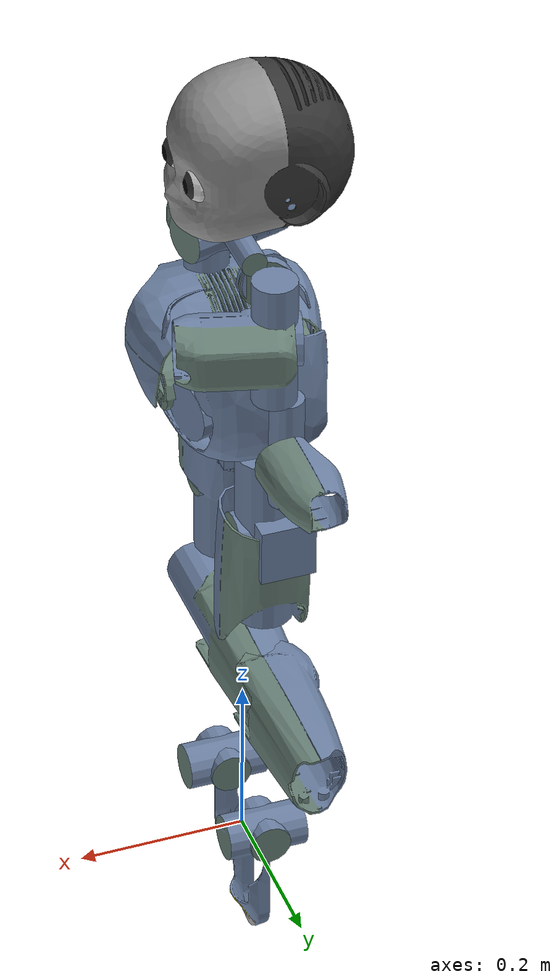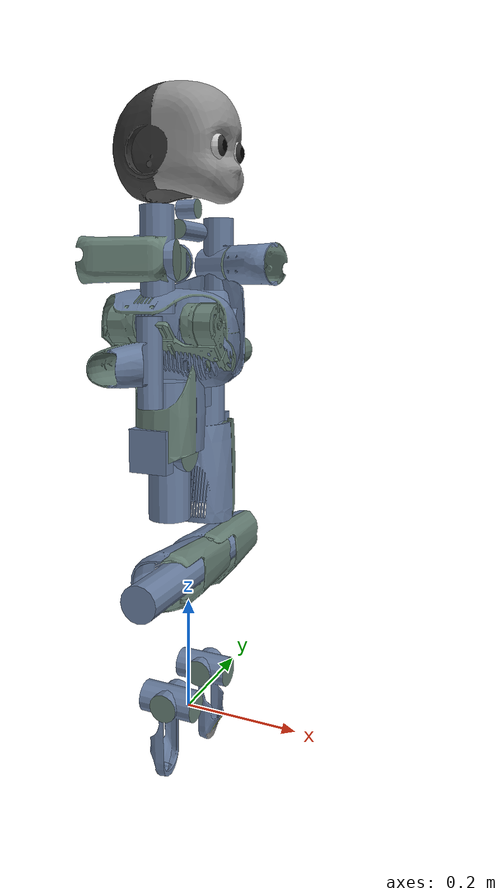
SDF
<?xml version='1.0'?>
<sdf version='1.5'>
  <model name='iCub'>
    <pose>0 0 0.6 0 0 3.14</pose>
    <link name='root_link'>
      <pose>0 0 0 0 -0 0</pose>
      <inertial>
        <pose>0 0 0 0 -0 0</pose>
        <mass>4.72</mass>
        <inertia>
          <ixx>0.01</ixx>
          <ixy>0</ixy>
          <ixz>0</ixz>
          <iyy>0.01</iyy>
          <iyz>0</iyz>
          <izz>0.01</izz>
        </inertia>
      </inertial>
      <collision name='root_link_collision'>
        <pose>0 0 0 0 -0 0</pose>
        <geometry>
          <mesh>
            <scale>1 1 1</scale>
            <uri>model://icub/meshes/collision/icub_simple_collision_root_link.dae</uri>
          </mesh>
        </geometry>
      </collision>
      <visual name='root_link_visual'>
        <pose>0 0 0 0 -0 0</pose>
        <geometry>
          <mesh>
            <scale>1 1 1</scale>
            <uri>model://icub/meshes/visual/icub_root_link.dae</uri>
          </mesh>
        </geometry>
      </visual>
    </link>
    <link name='l_hip_1'>
      <pose>0 -0.0681 -0.1199 2.65359e-06 1.57079 3.14159</pose>
      <inertial>
        <pose>0 -0.0782 0 0 -0 0</pose>
        <mass>0.754</mass>
        <inertia>
          <ixx>0.01</ixx>
          <ixy>2.059e-06</ixy>
          <ixz>1.451e-06</ixz>
          <iyy>0.01</iyy>
          <iyz>1.545e-06</iyz>
          <izz>0.01</izz>
        </inertia>
      </inertial>
      <collision name='l_hip_1_collision'>
        <pose>0 0 0 -0.785403 1.57079 -2.35619</pose>
        <geometry>
          <mesh>
            <scale>1 1 1</scale>
            <uri>model://icub/meshes/collision/icub_simple_collision_l_hip_1.dae</uri>
          </mesh>
        </geometry>
      </collision>
      <visual name='l_hip_1_visual'>
        <pose>0 0 0 -0.785403 1.57079 -2.35619</pose>
        <geometry>
          <mesh>
            <scale>1 1 1</scale>
            <uri>model://icub/meshes/visual/icub_l_hip_1.dae</uri>
          </mesh>
        </geometry>
      </visual>
    </link>
    <joint name='l_hip_pitch' type='revolute'>
      <child>l_hip_1</child>
      <parent>root_link</parent>
      <axis>
        <xyz>2.65359e-06 1 -9.74718e-12</xyz>
        <limit>
          <lower>-0.767945</lower>
          <upper>2.30383</upper>
          <effort>84</effort>
          <velocity>100</velocity>
        </limit>
        <dynamics>
          <damping>1</damping>
          <friction>0</friction>
          <spring_reference>0</spring_reference>
          <spring_stiffness>0</spring_stiffness>
        </dynamics>
        <use_parent_model_frame>1</use_parent_model_frame>
      </axis>
    </joint>
    <link name='l_hip_2'>
      <pose>0 -0.0681 -0.1199 3.14159 -7.34641e-06 3.14159</pose>
      <inertial>
        <pose>0 0 0.03045 0 -0 0</pose>
        <mass>0.526</mass>
        <inertia>
          <ixx>0.01</ixx>
          <ixy>-7.4e-08</ixy>
          <ixz>1.0835e-05</ixz>
          <iyy>0.01</iyy>
          <iyz>-6.2e-08</iyz>
          <izz>0.01</izz>
        </inertia>
      </inertial>
      <collision name='l_hip_2_collision'>
        <pose>0 0 0 0.785363 -1.57079 2.35623</pose>
        <geometry>
          <mesh>
            <scale>1 1 1</scale>
            <uri>model://icub/meshes/collision/icub_simple_collision_l_hip_2.dae</uri>
          </mesh>
        </geometry>
      </collision>
      <visual name='l_hip_2_visual'>
        <pose>0 0 0 0.785363 -1.57079 2.35623</pose>
        <geometry>
          <mesh>
            <scale>1 1 1</scale>
            <uri>model://icub/meshes/visual/icub_l_hip_2.dae</uri>
          </mesh>
        </geometry>
      </visual>
    </link>
    <joint name='l_hip_roll' type='revolute'>
      <child>l_hip_2</child>
      <parent>l_hip_1</parent>
      <axis>
        <xyz>-1 2.65359e-06 7.34641e-06</xyz>
        <limit>
          <lower>-0.296706</lower>
          <upper>2.07694</upper>
          <effort>84</effort>
          <velocity>100</velocity>
        </limit>
        <dynamics>
          <damping>1</damping>
          <friction>0</friction>
          <spring_reference>0</spring_reference>
          <spring_stiffness>0</spring_stiffness>
        </dynamics>
        <use_parent_model_frame>1</use_parent_model_frame>
      </axis>
    </joint>
    <link name='l_hip_3'>
      <pose>-4.88536e-07 -0.0680998 -0.1864 3.14159 -7.34641e-06 3.14159</pose>
      <inertial>
        <pose>0 0 0 0 -0 0</pose>
        <mass>0.1</mass>
        <inertia>
          <ixx>0.01</ixx>
          <ixy>0</ixy>
          <ixz>0</ixz>
          <iyy>0.01</iyy>
          <iyz>0</iyz>
          <izz>0.01</izz>
        </inertia>
      </inertial>
    </link>
    <joint name='l_leg_ft_sensor' type='revolute'>
      <child>l_hip_3</child>
      <parent>l_hip_2</parent>
      <axis>
        <xyz>0 0 0</xyz>
        <limit>
          <lower>0</lower>
          <upper>0</upper>
          <effort>0</effort>
          <velocity>0</velocity>
        </limit>
        <dynamics>
          <spring_reference>0</spring_reference>
          <spring_stiffness>0</spring_stiffness>
        </dynamics>
        <use_parent_model_frame>1</use_parent_model_frame>
      </axis>
      <sensor name='left_leg_ft' type='force_torque'>
        <always_on>1</always_on>
        <update_rate>100</update_rate>
        <pose>0 0 0 0 0 0</pose>
        <plugin name='left_leg_ft_plugin' filename='libgazebo_yarp_forcetorque.so'>
          <yarpConfigurationFile>model://icub/conf/FT/gazebo_icub_left_leg_ft.ini</yarpConfigurationFile>
        </plugin>
      </sensor>
    </joint>
    <link name='l_upper_leg'>
      <pose>0 -0.0681 -0.1199 1.57079 -7.34641e-06 3.14159</pose>
      <inertial>
        <pose>0.00144 -0.15943 -0.00039 0 -0 0</pose>
        <mass>2.175</mass>
        <inertia>
          <ixx>0.01</ixx>
          <ixy>-6.726e-05</ixy>
          <ixz>2.267e-06</ixz>
          <iyy>0.01</iyy>
          <iyz>3.63726e-05</iyz>
          <izz>0.01</izz>
        </inertia>
      </inertial>
      <collision name='l_upper_leg_collision'>
        <pose>0 0 0 -2.67797 1.57079 -1.10716</pose>
        <geometry>
          <mesh>
            <scale>1 1 1</scale>
            <uri>model://icub/meshes/collision/icub_simple_collision_l_thigh.dae</uri>
          </mesh>
        </geometry>
      </collision>
      <visual name='l_upper_leg_visual'>
        <pose>0 0 0 -2.67797 1.57079 -1.10716</pose>
        <geometry>
          <mesh>
            <scale>1 1 1</scale>
            <uri>model://icub/meshes/visual/icub_l_thigh.dae</uri>
          </mesh>
        </geometry>
      </visual>
    </link>
    <joint name='l_hip_yaw' type='revolute'>
      <child>l_upper_leg</child>
      <parent>l_hip_3</parent>
      <axis>
        <xyz>7.34639e-06 -6.3268e-06 1</xyz>
        <limit>
          <lower>-1.37881</lower>
          <upper>1.37881</upper>
          <effort>40</effort>
          <velocity>100</velocity>
        </limit>
        <dynamics>
          <damping>1</damping>
          <friction>0</friction>
          <spring_reference>0</spring_reference>
          <spring_stiffness>0</spring_stiffness>
        </dynamics>
        <use_parent_model_frame>1</use_parent_model_frame>
      </axis>
    </joint>
    <link name='l_lower_leg'>
      <pose>-1.64265e-06 -0.0680986 -0.3435 2.09198 -1.57078 -0.521189</pose>
      <inertial>
        <pose>-0.1071 0.00182 0.00211 0 -0 0</pose>
        <mass>1.264</mass>
        <inertia>
          <ixx>0.01</ixx>
          <ixy>-0.000185699</ixy>
          <ixz>-6.3147e-05</ixz>
          <iyy>0.01</iyy>
          <iyz>7.86e-07</iyz>
          <izz>0.01</izz>
        </inertia>
      </inertial>
      <collision name='l_lower_leg_collision'>
        <pose>5.55112e-17 2.28232e-12 2.2823e-12 -3.14159 -2.33487e-16 1.5708</pose>
        <geometry>
          <mesh>
            <scale>1 1 1</scale>
            <uri>model://icub/meshes/collision/icub_simple_collision_l_shank.dae</uri>
          </mesh>
        </geometry>
      </collision>
      <visual name='l_lower_leg_visual'>
        <pose>5.55112e-17 2.28232e-12 2.2823e-12 -3.14159 -2.33487e-16 1.5708</pose>
        <geometry>
          <mesh>
            <scale>1 1 1</scale>
            <uri>model://icub/meshes/visual/icub_l_shank.dae</uri>
          </mesh>
        </geometry>
      </visual>
    </link>
    <joint name='l_knee' type='revolute'>
      <child>l_lower_leg</child>
      <parent>l_upper_leg</parent>
      <axis>
        <xyz>5.30723e-06 1 6.32676e-06</xyz>
        <limit>
          <lower>-2.18166</lower>
          <upper>0.401426</upper>
          <effort>30</effort>
          <velocity>100</velocity>
        </limit>
        <dynamics>
          <damping>1</damping>
          <friction>0</friction>
          <spring_reference>0</spring_reference>
          <spring_stiffness>0</spring_stiffness>
        </dynamics>
        <use_parent_model_frame>1</use_parent_model_frame>
      </axis>
    </joint>
    <link name='l_ankle_1'>
      <pose>-3.98983e-06 -0.0680972 -0.5565 0.52118 -1.57078 -0.521189</pose>
      <inertial>
        <pose>-0.0054 0.00163 0.0172 0 -0 0</pose>
        <mass>0.746</mass>
        <inertia>
          <ixx>0.01</ixx>
          <ixy>-7.081e-06</ixy>
          <ixz>4.1421e-05</ixz>
          <iyy>0.01</iyy>
          <iyz>2.0817e-05</iyz>
          <izz>0.01</izz>
        </inertia>
      </inertial>
      <collision name='l_ankle_1_collision'>
        <pose>1.11022e-16 -5.54343e-12 4.45647e-12 1.5708 1.53106e-11 1.53105e-11</pose>
        <geometry>
          <mesh>
            <scale>1 1 1</scale>
            <uri>model://icub/meshes/collision/icub_simple_collision_l_ankle_1.dae</uri>
          </mesh>
        </geometry>
      </collision>
      <visual name='l_ankle_1_visual'>
        <pose>1.11022e-16 -5.54343e-12 4.45647e-12 1.5708 1.53106e-11 1.53105e-11</pose>
        <geometry>
          <mesh>
            <scale>1 1 1</scale>
            <uri>model://icub/meshes/visual/icub_l_ankle_1.dae</uri>
          </mesh>
        </geometry>
      </visual>
    </link>
    <joint name='l_ankle_pitch' type='revolute'>
      <child>l_ankle_1</child>
      <parent>l_lower_leg</parent>
      <axis>
        <xyz>-8.98043e-06 -1 -6.32672e-06</xyz>
        <limit>
          <lower>-0.733038</lower>
          <upper>0.366519</upper>
          <effort>24</effort>
          <velocity>100</velocity>
        </limit>
        <dynamics>
          <damping>1</damping>
          <friction>0</friction>
          <spring_reference>0</spring_reference>
          <spring_stiffness>0</spring_stiffness>
        </dynamics>
        <use_parent_model_frame>1</use_parent_model_frame>
      </axis>
    </joint>
    <link name='l_ankle_2'>
      <pose>-3.98983e-06 -0.0680972 -0.5565 3.14159 -7.34645e-06 3.14158</pose>
      <inertial>
        <pose>0 0 0.037 0 -0 0</pose>
        <mass>0.2675</mass>
        <inertia>
          <ixx>0.01</ixx>
          <ixy>0</ixy>
          <ixz>0</ixz>
          <iyy>0.01</iyy>
          <iyz>0</iyz>
          <izz>0.01</izz>
        </inertia>
      </inertial>
    </link>
    <joint name='l_ankle_roll' type='revolute'>
      <child>l_ankle_2</child>
      <parent>l_ankle_1</parent>
      <axis>
        <xyz>-1 8.98038e-06 7.34645e-06</xyz>
        <limit>
          <lower>-0.418879</lower>
          <upper>0.418879</upper>
          <effort>11</effort>
          <velocity>100</velocity>
        </limit>
        <dynamics>
          <damping>1</damping>
          <friction>0</friction>
          <spring_reference>0</spring_reference>
          <spring_stiffness>0</spring_stiffness>
        </dynamics>
        <use_parent_model_frame>1</use_parent_model_frame>
      </axis>
    </joint>
    <link name='l_foot'>
      <pose>-4.26164e-06 -0.068097 -0.5935 3.14159 -7.34645e-06 3.14158</pose>
      <inertial>
        <pose>0.024069 -0.000613931 -0.0284154 0 -0 0</pose>
        <mass>0.5935</mass>
        <inertia>
          <ixx>0.01</ixx>
          <ixy>-4.51893e-06</ixy>
          <ixz>0.000567785</ixz>
          <iyy>0.01</iyy>
          <iyz>-6.62361e-07</iyz>
          <izz>0.01</izz>
        </inertia>
      </inertial>
      <collision name='l_foot_collision'>
        <pose>0.03 0 -0.01 0 -0 0</pose>
        <geometry>
          <box>
            <size>0.15 0.07 0.03</size>
          </box>
        </geometry>
        <max_contacts>4</max_contacts>
        <surface>
          <contact>
            <ode>
              <soft_erp>0.2</soft_erp>
              <soft_cfm>0</soft_cfm>
              <kp>18000000</kp>
              <kd>100</kd>
              <max_vel>100</max_vel>
              <min_depth>0.0001</min_depth>
            </ode>
          </contact>
          <friction>
            <ode>
              <mu>1</mu>
              <mu2>1</mu2>
              <fdir1>0 0 0</fdir1>
              <slip1>0</slip1>
              <slip2>0</slip2>
            </ode>
          </friction>
          <bounce>
            <restitution_coefficient>0</restitution_coefficient>
            <threshold>100000</threshold>
          </bounce>
        </surface>
      </collision>
      <visual name='l_foot_visual'>
        <pose>4.45647e-12 -5.54343e-12 -0.037 -0.785403 1.57079 -0.785403</pose>
        <geometry>
          <mesh>
            <scale>1 1 1</scale>
            <uri>model://icub/meshes/visual/icub_l_foot.dae</uri>
          </mesh>
        </geometry>
      </visual>
    </link>
    <joint name='l_foot_ft_sensor' type='revolute'>
      <child>l_foot</child>
      <parent>l_ankle_2</parent>
      <axis>
        <xyz>0 0 0</xyz>
        <limit>
          <lower>0</lower>
          <upper>0</upper>
          <effort>0</effort>
          <velocity>0</velocity>
        </limit>
        <dynamics>
          <spring_reference>0</spring_reference>
          <spring_stiffness>0</spring_stiffness>
        </dynamics>
        <use_parent_model_frame>1</use_parent_model_frame>
      </axis>
      <sensor name='left_foot_ft' type='force_torque'>
        <always_on>1</always_on>
        <update_rate>100</update_rate>
        <pose>0 0 0 0 0 0</pose>
        <plugin name='left_foot_ft_plugin' filename='libgazebo_yarp_forcetorque.so'>
          <yarpConfigurationFile>model://icub/conf/FT/gazebo_icub_left_foot_ft.ini</yarpConfigurationFile>
        </plugin>
      </sensor>
    </joint>
    <link name='r_hip_1'>
      <pose>0 0.0681 -0.1199 3.14159 1.57079 -3.14159</pose>
      <inertial>
        <pose>0 -0.0782 0 0 -0 0</pose>
        <mass>0.754</mass>
        <inertia>
          <ixx>0.01</ixx>
          <ixy>0</ixy>
          <ixz>0</ixz>
          <iyy>0.01</iyy>
          <iyz>0</iyz>
          <izz>0.01</izz>
        </inertia>
      </inertial>
      <collision name='r_hip_1_collision'>
        <pose>0 0 0 1.76819 -1.57079 2.76109</pose>
        <geometry>
          <mesh>
            <scale>1 1 1</scale>
            <uri>model://icub/meshes/collision/icub_simple_collision_r_hip_1.dae</uri>
          </mesh>
        </geometry>
      </collision>
      <visual name='r_hip_1_visual'>
        <pose>0 0 0 1.76819 -1.57079 2.76109</pose>
        <geometry>
          <mesh>
            <scale>1 1 1</scale>
            <uri>model://icub/meshes/visual/icub_r_hip_1.dae</uri>
          </mesh>
        </geometry>
      </visual>
    </link>
    <joint name='r_hip_pitch' type='revolute'>
      <child>r_hip_1</child>
      <parent>root_link</parent>
      <axis>
        <xyz>5.7211e-18 1 -1.22967e-22</xyz>
        <limit>
          <lower>-0.767945</lower>
          <upper>2.30383</upper>
          <effort>84</effort>
          <velocity>100</velocity>
        </limit>
        <dynamics>
          <damping>1</damping>
          <friction>0</friction>
          <spring_reference>0</spring_reference>
          <spring_stiffness>0</spring_stiffness>
        </dynamics>
        <use_parent_model_frame>1</use_parent_model_frame>
      </axis>
    </joint>
    <link name='r_hip_2'>
      <pose>0 0.0681 -0.1199 -3.14159 -7.34641e-06 -3.14159</pose>
      <inertial>
        <pose>0 0 0.03045 0 -0 0</pose>
        <mass>0.526</mass>
        <inertia>
          <ixx>0.01</ixx>
          <ixy>0</ixy>
          <ixz>0</ixz>
          <iyy>0.01</iyy>
          <iyz>0</iyz>
          <izz>0.01</izz>
        </inertia>
      </inertial>
      <collision name='r_hip_2_collision'>
        <pose>0 0 0 -2.35627 -1.57079 2.35627</pose>
        <geometry>
          <mesh>
            <scale>1 1 1</scale>
            <uri>model://icub/meshes/collision/icub_simple_collision_r_hip_2.dae</uri>
          </mesh>
        </geometry>
      </collision>
      <visual name='r_hip_2_visual'>
        <pose>0 0 0 -2.35627 -1.57079 2.35627</pose>
        <geometry>
          <mesh>
            <scale>1 1 1</scale>
            <uri>model://icub/meshes/visual/icub_r_hip_2.dae</uri>
          </mesh>
        </geometry>
      </visual>
    </link>
    <joint name='r_hip_roll' type='revolute'>
      <child>r_hip_2</child>
      <parent>r_hip_1</parent>
      <axis>
        <xyz>1 5.55111e-17 -7.34641e-06</xyz>
        <limit>
          <lower>-0.296706</lower>
          <upper>2.07694</upper>
          <effort>84</effort>
          <velocity>100</velocity>
        </limit>
        <dynamics>
          <damping>1</damping>
          <friction>0</friction>
          <spring_reference>0</spring_reference>
          <spring_stiffness>0</spring_stiffness>
        </dynamics>
        <use_parent_model_frame>1</use_parent_model_frame>
      </axis>
    </joint>
    <link name='r_hip_3'>
      <pose>-4.88536e-07 0.0681 -0.1864 -3.14159 -7.34641e-06 -3.14159</pose>
      <inertial>
        <pose>0 0 0 0 -0 0</pose>
        <mass>0.1</mass>
        <inertia>
          <ixx>0.01</ixx>
          <ixy>0</ixy>
          <ixz>0</ixz>
          <iyy>0.01</iyy>
          <iyz>0</iyz>
          <izz>0.01</izz>
        </inertia>
      </inertial>
    </link>
    <joint name='r_leg_ft_sensor' type='revolute'>
      <child>r_hip_3</child>
      <parent>r_hip_2</parent>
      <axis>
        <xyz>0 0 -0</xyz>
        <limit>
          <lower>0</lower>
          <upper>0</upper>
          <effort>0</effort>
          <velocity>0</velocity>
        </limit>
        <dynamics>
          <spring_reference>0</spring_reference>
          <spring_stiffness>0</spring_stiffness>
        </dynamics>
        <use_parent_model_frame>1</use_parent_model_frame>
      </axis>
      <sensor name='right_leg_ft' type='force_torque'>
        <always_on>1</always_on>
        <update_rate>100</update_rate>
        <pose>0 0 0 0 0 0</pose>
        <plugin name='right_leg_ft_plugin' filename='libgazebo_yarp_forcetorque.so'>
          <yarpConfigurationFile>model://icub/conf/FT/gazebo_icub_right_leg_ft.ini</yarpConfigurationFile>
        </plugin>
      </sensor>
    </joint>
    <link name='r_upper_leg'>
      <pose>0 0.0681 -0.1199 1.57079 -7.34641e-06 3.14159</pose>
      <inertial>
        <pose>0.00144 -0.15943 0.00039 0 -0 0</pose>
        <mass>2.175</mass>
        <inertia>
          <ixx>0.01</ixx>
          <ixy>0</ixy>
          <ixz>0</ixz>
          <iyy>0.01</iyy>
          <iyz>-2.71051e-20</iyz>
          <izz>0.01</izz>
        </inertia>
      </inertial>
      <collision name='r_upper_leg_collision'>
        <pose>0 0 0 1.57087 -1.57079 -7.26536e-05</pose>
        <geometry>
          <mesh>
            <scale>1 1 1</scale>
            <uri>model://icub/meshes/collision/icub_simple_collision_r_thigh.dae</uri>
          </mesh>
        </geometry>
      </collision>
      <visual name='r_upper_leg_visual'>
        <pose>0 0 0 1.57087 -1.57079 -7.26536e-05</pose>
        <geometry>
          <mesh>
            <scale>1 1 1</scale>
            <uri>model://icub/meshes/visual/icub_r_thigh.dae</uri>
          </mesh>
        </geometry>
      </visual>
    </link>
    <joint name='r_hip_yaw' type='revolute'>
      <child>r_upper_leg</child>
      <parent>r_hip_3</parent>
      <axis>
        <xyz>-7.34641e-06 3.67321e-06 -1</xyz>
        <limit>
          <lower>-1.37881</lower>
          <upper>1.37881</upper>
          <effort>40</effort>
          <velocity>100</velocity>
        </limit>
        <dynamics>
          <damping>1</damping>
          <friction>0</friction>
          <spring_reference>0</spring_reference>
          <spring_stiffness>0</spring_stiffness>
        </dynamics>
        <use_parent_model_frame>1</use_parent_model_frame>
      </axis>
    </joint>
    <link name='r_lower_leg'>
      <pose>-1.64266e-06 0.0681008 -0.3435 1.89254 -1.57078 -0.321751</pose>
      <inertial>
        <pose>-0.1071 0.00182 -0.00211 0 -0 0</pose>
        <mass>1.264</mass>
        <inertia>
          <ixx>0.01</ixx>
          <ixy>5.42101e-20</ixy>
          <ixz>-5.42101e-20</ixz>
          <iyy>0.01</iyy>
          <iyz>8.47033e-22</iyz>
          <izz>0.01</izz>
        </inertia>
      </inertial>
      <collision name='r_lower_leg_collision'>
        <pose>5.55112e-17 2.28232e-12 -8.32667e-17 3.14159 -1.14426e-17 1.5708</pose>
        <geometry>
          <mesh>
            <scale>1 1 1</scale>
            <uri>model://icub/meshes/collision/icub_simple_collision_r_shank.dae</uri>
          </mesh>
        </geometry>
      </collision>
      <visual name='r_lower_leg_visual'>
        <pose>5.55112e-17 2.28232e-12 -8.32667e-17 3.14159 -1.14426e-17 1.5708</pose>
        <geometry>
          <mesh>
            <scale>1 1 1</scale>
            <uri>model://icub/meshes/visual/icub_r_shank.dae</uri>
          </mesh>
        </geometry>
      </visual>
    </link>
    <joint name='r_knee' type='revolute'>
      <child>r_lower_leg</child>
      <parent>r_upper_leg</parent>
      <axis>
        <xyz>2.65362e-06 1 3.67318e-06</xyz>
        <limit>
          <lower>-2.18166</lower>
          <upper>0.401426</upper>
          <effort>30</effort>
          <velocity>100</velocity>
        </limit>
        <dynamics>
          <damping>1</damping>
          <friction>0</friction>
          <spring_reference>0</spring_reference>
          <spring_stiffness>0</spring_stiffness>
        </dynamics>
        <use_parent_model_frame>1</use_parent_model_frame>
      </axis>
    </joint>
    <link name='r_ankle_1'>
      <pose>-3.98984e-06 0.0681016 -0.5565 -2.81984 -1.57078 -0.321751</pose>
      <inertial>
        <pose>-0.0054 0.00163 -0.0172 0 -0 0</pose>
        <mass>0.746</mass>
        <inertia>
          <ixx>0.01</ixx>
          <ixy>-1.69407e-21</ixy>
          <ixz>1.35525e-20</ixz>
          <iyy>0.01</iyy>
          <iyz>3.38813e-21</iyz>
          <izz>0.01</izz>
        </inertia>
      </inertial>
      <collision name='r_ankle_1_collision'>
        <pose>1.11022e-16 -1.08717e-12 -4.45647e-12 -1.5708 -1.53106e-11 5.10376e-12</pose>
        <geometry>
          <mesh>
            <scale>1 1 1</scale>
            <uri>model://icub/meshes/collision/icub_simple_collision_r_ankle_1.dae</uri>
          </mesh>
        </geometry>
      </collision>
      <visual name='r_ankle_1_visual'>
        <pose>1.11022e-16 -1.08717e-12 -4.45647e-12 -1.5708 -1.53106e-11 5.10376e-12</pose>
        <geometry>
          <mesh>
            <scale>1 1 1</scale>
            <uri>model://icub/meshes/visual/icub_r_ankle_1.dae</uri>
          </mesh>
        </geometry>
      </visual>
    </link>
    <joint name='r_ankle_pitch' type='revolute'>
      <child>r_ankle_1</child>
      <parent>r_lower_leg</parent>
      <axis>
        <xyz>1.01959e-06 -1 -3.67322e-06</xyz>
        <limit>
          <lower>-0.733038</lower>
          <upper>0.366519</upper>
          <effort>24</effort>
          <velocity>100</velocity>
        </limit>
        <dynamics>
          <damping>1</damping>
          <friction>0</friction>
          <spring_reference>0</spring_reference>
          <spring_stiffness>0</spring_stiffness>
        </dynamics>
        <use_parent_model_frame>1</use_parent_model_frame>
      </axis>
    </joint>
    <link name='r_ankle_2'>
      <pose>-3.98984e-06 0.0681016 -0.5565 3.14159 -1.4236e-05 -3.14159</pose>
      <inertial>
        <pose>0 0 0.037 0 -0 0</pose>
        <mass>0.2675</mass>
        <inertia>
          <ixx>0.01</ixx>
          <ixy>0</ixy>
          <ixz>0</ixz>
          <iyy>0.01</iyy>
          <iyz>0</iyz>
          <izz>0.01</izz>
        </inertia>
      </inertial>
    </link>
    <joint name='r_ankle_roll' type='revolute'>
      <child>r_ankle_2</child>
      <parent>r_ankle_1</parent>
      <axis>
        <xyz>1 2.79362e-06 -1.4236e-05</xyz>
        <limit>
          <lower>-0.418879</lower>
          <upper>0.418879</upper>
          <effort>11</effort>
          <velocity>100</velocity>
        </limit>
        <dynamics>
          <damping>1</damping>
          <friction>0</friction>
          <spring_reference>0</spring_reference>
          <spring_stiffness>0</spring_stiffness>
        </dynamics>
        <use_parent_model_frame>1</use_parent_model_frame>
      </axis>
    </joint>
    <link name='r_foot'>
      <pose>-4.51657e-06 0.0681019 -0.5935 3.14159 -1.4236e-05 -3.14159</pose>
      <inertial>
        <pose>0.024069 0.000613931 -0.0284154 0 -0 0</pose>
        <mass>0.5935</mass>
        <inertia>
          <ixx>0.01</ixx>
          <ixy>4.51893e-06</ixy>
          <ixz>0.000567784</ixz>
          <iyy>0.01</iyy>
          <iyz>6.62535e-07</iyz>
          <izz>0.01</izz>
        </inertia>
      </inertial>
      <collision name='r_foot_collision'>
        <pose>0.03 0 -0.01 0 -0 0</pose>
        <geometry>
          <box>
            <size>0.15 0.07 0.03</size>
          </box>
        </geometry>
        <max_contacts>4</max_contacts>
        <surface>
          <contact>
            <ode>
              <soft_erp>0.2</soft_erp>
              <soft_cfm>0</soft_cfm>
              <kp>18000000</kp>
              <kd>100</kd>
              <max_vel>100</max_vel>
              <min_depth>0.0001</min_depth>
            </ode>
          </contact>
          <friction>
            <ode>
              <mu>1</mu>
              <mu2>1</mu2>
              <fdir1>0 0 0</fdir1>
              <slip1>0</slip1>
              <slip2>0</slip2>
            </ode>
          </friction>
          <bounce>
            <restitution_coefficient>0</restitution_coefficient>
            <threshold>100000</threshold>
          </bounce>
        </surface>
      </collision>
      <visual name='r_foot_visual'>
        <pose>4.45647e-12 1.08717e-12 -0.037 -2.81983 1.57079 0.321763</pose>
        <geometry>
          <mesh>
            <scale>1 1 1</scale>
            <uri>model://icub/meshes/visual/icub_r_foot.dae</uri>
          </mesh>
        </geometry>
      </visual>
    </link>
    <joint name='r_foot_ft_sensor' type='revolute'>
      <child>r_foot</child>
      <parent>r_ankle_2</parent>
      <axis>
        <xyz>0 0 0</xyz>
        <limit>
          <lower>0</lower>
          <upper>0</upper>
          <effort>0</effort>
          <velocity>0</velocity>
        </limit>
        <dynamics>
          <spring_reference>0</spring_reference>
          <spring_stiffness>0</spring_stiffness>
        </dynamics>
        <use_parent_model_frame>1</use_parent_model_frame>
      </axis>
      <sensor name='right_foot_ft' type='force_torque'>
        <always_on>1</always_on>
        <update_rate>100</update_rate>
        <pose>0 0 0 0 0 0</pose>
        <plugin name='right_foot_ft_plugin' filename='libgazebo_yarp_forcetorque.so'>
          <yarpConfigurationFile>model://icub/conf/FT/gazebo_icub_right_foot_ft.ini</yarpConfigurationFile>
        </plugin>
      </sensor>
    </joint>
    <link name='torso_1'>
      <pose>0 0 0 3.14159 -1.57079 -2.65359e-06</pose>
      <inertial>
        <pose>0 0 0 0 -0 0</pose>
        <mass>0.1</mass>
        <inertia>
          <ixx>0.01</ixx>
          <ixy>-4.263e-05</ixy>
          <ixz>-3.889e-08</ixz>
          <iyy>0.01</iyy>
          <iyz>0</iyz>
          <izz>0.01</izz>
        </inertia>
      </inertial>
      <collision name='torso_1_collision'>
        <pose>0 0 0 -1.5708 5.10314e-12 1.11022e-16</pose>
        <geometry>
          <mesh>
            <scale>1 1 1</scale>
            <uri>model://icub/meshes/collision/icub_simple_collision_lap_belt_1.dae</uri>
          </mesh>
        </geometry>
      </collision>
      <visual name='torso_1_visual'>
        <pose>0 0 0 -1.5708 5.10314e-12 1.11022e-16</pose>
        <geometry>
          <mesh>
            <scale>1 1 1</scale>
            <uri>model://icub/meshes/visual/icub_lap_belt_1.dae</uri>
          </mesh>
        </geometry>
      </visual>
    </link>
    <joint name='torso_pitch' type='revolute'>
      <child>torso_1</child>
      <parent>root_link</parent>
      <axis>
        <xyz>-2.65359e-06 -1 -1.05879e-22</xyz>
        <limit>
          <lower>-0.383972</lower>
          <upper>1.46608</upper>
          <effort>36</effort>
          <velocity>100</velocity>
        </limit>
        <dynamics>
          <damping>1</damping>
          <friction>0</friction>
          <spring_reference>0</spring_reference>
          <spring_stiffness>0</spring_stiffness>
        </dynamics>
        <use_parent_model_frame>1</use_parent_model_frame>
      </axis>
    </joint>
    <link name='torso_2'>
      <pose>1.17543e-07 -3.1191e-13 0.032 -3.14159 3.67321e-06 1.57079</pose>
      <inertial>
        <pose>0 0 0 0 -0 0</pose>
        <mass>0.1</mass>
        <inertia>
          <ixx>0.01</ixx>
          <ixy>-1.923e-06</ixy>
          <ixz>5.095e-05</ixz>
          <iyy>0.01</iyy>
          <iyz>-3.849e-07</iyz>
          <izz>0.01</izz>
        </inertia>
      </inertial>
    </link>
    <joint name='torso_roll' type='revolute'>
      <child>torso_2</child>
      <parent>torso_1</parent>
      <axis>
        <xyz>1 -2.6536e-06 -7.34641e-06</xyz>
        <limit>
          <lower>-0.680678</lower>
          <upper>0.680678</upper>
          <effort>80</effort>
          <velocity>100</velocity>
        </limit>
        <dynamics>
          <damping>1</damping>
          <friction>0</friction>
          <spring_reference>0</spring_reference>
          <spring_stiffness>0</spring_stiffness>
        </dynamics>
        <use_parent_model_frame>1</use_parent_model_frame>
      </axis>
    </joint>
    <link name='chest'>
      <pose>-0.00549988 1.45945e-08 0.032 1.5708 -7.34642e-06 -3.14159</pose>
      <inertial>
        <pose>0.00222898 0.075 -1.18362e-17 0 -0 0</pose>
        <mass>4.81</mass>
        <inertia>
          <ixx>0.07472</ixx>
          <ixy>-3.6e-06</ixy>
          <ixz>-4.705e-05</ixz>
          <iyy>0.08145</iyy>
          <iyz>0.004567</iyz>
          <izz>0.01306</izz>
        </inertia>
      </inertial>
      <collision name='chest_collision'>
        <pose>-0.0055 -6.93889e-18 -3.55271e-18 -1.10717 -1.57079 2.67798</pose>
        <geometry>
          <mesh>
            <scale>1 1 1</scale>
            <uri>model://icub/meshes/collision/icub_simple_collision_chest.dae</uri>
          </mesh>
        </geometry>
      </collision>
      <visual name='chest_visual'>
        <pose>-0.0055 -6.93889e-18 -3.55271e-18 -1.10717 -1.57079 2.67798</pose>
        <geometry>
          <mesh>
            <scale>1 1 1</scale>
            <uri>model://icub/meshes/visual/icub_chest.dae</uri>
          </mesh>
        </geometry>
      </visual>
    </link>
    <joint name='torso_yaw' type='revolute'>
      <child>chest</child>
      <parent>torso_2</parent>
      <axis>
        <xyz>-7.34642e-06 1.94942e-11 -1</xyz>
        <limit>
          <lower>-1.02974</lower>
          <upper>1.02974</upper>
          <effort>80</effort>
          <velocity>100</velocity>
        </limit>
        <dynamics>
          <damping>1</damping>
          <friction>0</friction>
          <spring_reference>0</spring_reference>
          <spring_stiffness>0</spring_stiffness>
        </dynamics>
        <use_parent_model_frame>1</use_parent_model_frame>
      </axis>
    </joint>
    <link name='l_shoulder_1'>
      <pose>-0.0107487 -0.11026 0.1753 -0.261794 -1.57079 -1.42917e-06</pose>
      <inertial>
        <pose>-5e-06 0.0187 -0.00119 0 -0 0</pose>
        <mass>0.189</mass>
        <inertia>
          <ixx>0.01</ixx>
          <ixy>9e-09</ixy>
          <ixz>0</ixz>
          <iyy>0.01</iyy>
          <iyz>-1.7e-08</iyz>
          <izz>0.01</izz>
        </inertia>
      </inertial>
      <collision name='l_shoulder_1_collision'>
        <pose>3.08642e-14 0.109285 -0.00521101 -0.301063 1.57079 -1.87186</pose>
        <geometry>
          <mesh>
            <scale>1 1 1</scale>
            <uri>model://icub/meshes/collision/icub_simple_collision_l_shoulder_1.dae</uri>
          </mesh>
        </geometry>
      </collision>
      <visual name='l_shoulder_1_visual'>
        <pose>3.08642e-14 0.109285 -0.00521101 -0.301063 1.57079 -1.87186</pose>
        <geometry>
          <mesh>
            <scale>1 1 1</scale>
            <uri>model://icub/meshes/visual/icub_l_shoulder_1.dae</uri>
          </mesh>
        </geometry>
      </visual>
    </link>
    <joint name='l_shoulder_pitch' type='revolute'>
      <child>l_shoulder_1</child>
      <parent>chest</parent>
      <axis>
        <xyz>-0.258815 -0.965927 2.85203e-06</xyz>
        <limit>
          <lower>-1.65806</lower>
          <upper>0.0872665</upper>
          <effort>84</effort>
          <velocity>100</velocity>
        </limit>
        <dynamics>
          <damping>1</damping>
          <friction>0</friction>
          <spring_reference>0</spring_reference>
          <spring_stiffness>0</spring_stiffness>
        </dynamics>
        <use_parent_model_frame>1</use_parent_model_frame>
      </axis>
    </joint>
    <link name='l_shoulder_2'>
      <pose>-0.0107487 -0.11026 0.1753 3.14159 8.21174e-07 -1.83259</pose>
      <inertial>
        <pose>9.4e-05 -0.00627 0.0166 0 -0 0</pose>
        <mass>0.179</mass>
        <inertia>
          <ixx>0.01</ixx>
          <ixy>4.66e-07</ixy>
          <ixz>3.65e-07</ixz>
          <iyy>0.01</iyy>
          <iyz>-2.0524e-05</iyz>
          <izz>0.01</izz>
        </inertia>
      </inertial>
      <collision name='l_shoulder_2_collision'>
        <pose>-0.00154529 -0.00521101 -1.11181e-12 -2.14033 1.57079 -0.569533</pose>
        <geometry>
          <mesh>
            <scale>1 1 1</scale>
            <uri>model://icub/meshes/collision/icub_simple_collision_l_shoulder_2.dae</uri>
          </mesh>
        </geometry>
      </collision>
      <visual name='l_shoulder_2_visual'>
        <pose>-0.00154529 -0.00521101 -1.11181e-12 -2.14033 1.57079 -0.569533</pose>
        <geometry>
          <mesh>
            <scale>1 1 1</scale>
            <uri>model://icub/meshes/visual/icub_l_shoulder_2.dae</uri>
          </mesh>
        </geometry>
      </visual>
    </link>
    <joint name='l_shoulder_roll' type='revolute'>
      <child>l_shoulder_2</child>
      <parent>l_shoulder_1</parent>
      <axis>
        <xyz>-0.965927 0.258815 6.97095e-06</xyz>
        <limit>
          <lower>0</lower>
          <upper>2.80649</upper>
          <effort>84</effort>
          <velocity>100</velocity>
        </limit>
        <dynamics>
          <damping>1</damping>
          <friction>0</friction>
          <spring_reference>0</spring_reference>
          <spring_stiffness>0</spring_stiffness>
        </dynamics>
        <use_parent_model_frame>1</use_parent_model_frame>
      </axis>
    </joint>
    <link name='l_shoulder_3'>
      <pose>-0.0107487 -0.11026 0.1753 3.14159 -6.5209e-06 -3.14159</pose>
      <inertial>
        <pose>0.00559398 9.77357e-05 0.0501346 0 -0 0</pose>
        <mass>0.156157</mass>
        <inertia>
          <ixx>0.01</ixx>
          <ixy>-5.662e-08</ixy>
          <ixz>-4.3618e-06</ixz>
          <iyy>0.01</iyy>
          <iyz>-7.42844e-07</iyz>
          <izz>0.01</izz>
        </inertia>
      </inertial>
    </link>
    <joint name='l_shoulder_yaw' type='revolute'>
      <child>l_shoulder_3</child>
      <parent>l_shoulder_2</parent>
      <axis>
        <xyz>-6.5209e-06 2.59738e-06 -1</xyz>
        <limit>
          <lower>-0.645772</lower>
          <upper>1.74533</upper>
          <effort>34</effort>
          <velocity>100</velocity>
        </limit>
        <dynamics>
          <damping>1</damping>
          <friction>0</friction>
          <spring_reference>0</spring_reference>
          <spring_stiffness>0</spring_stiffness>
        </dynamics>
        <use_parent_model_frame>1</use_parent_model_frame>
      </axis>
    </joint>
    <link name='l_upper_arm'>
      <pose>-0.0257492 -0.11026 0.1073 3.14159 -6.5209e-06 -3.14159</pose>
      <inertial>
        <pose>-0.000156 -9.87e-05 0.0298 0 -0 0</pose>
        <mass>0.727843</mass>
        <inertia>
          <ixx>0.01</ixx>
          <ixy>-1.08e-06</ixy>
          <ixz>-2.29e-06</ixz>
          <iyy>0.01</iyy>
          <iyz>3.57e-06</iyz>
          <izz>0.01</izz>
        </inertia>
      </inertial>
      <collision name='l_upper_arm_collision'>
        <pose>-0.0204334 0.000143922 -0.068 1.15274e-11 4.92958e-12 -1.309</pose>
        <geometry>
          <mesh>
            <scale>1 1 1</scale>
            <uri>model://icub/meshes/collision/icub_simple_collision_l_arm.dae</uri>
          </mesh>
        </geometry>
      </collision>
      <visual name='l_upper_arm_visual'>
        <pose>-0.0204334 0.000143922 -0.068 1.15274e-11 4.92958e-12 -1.309</pose>
        <geometry>
          <mesh>
            <scale>1 1 1</scale>
            <uri>model://icub/meshes/visual/icub_l_arm.dae</uri>
          </mesh>
        </geometry>
      </visual>
    </link>
    <joint name='l_arm_ft_sensor' type='revolute'>
      <child>l_upper_arm</child>
      <parent>l_shoulder_3</parent>
      <axis>
        <xyz>-0 0 0</xyz>
        <limit>
          <lower>0</lower>
          <upper>0</upper>
          <effort>0</effort>
          <velocity>0</velocity>
        </limit>
        <dynamics>
          <spring_reference>0</spring_reference>
          <spring_stiffness>0</spring_stiffness>
        </dynamics>
        <use_parent_model_frame>1</use_parent_model_frame>
      </axis>
      <sensor name='left_arm_ft' type='force_torque'>
        <always_on>1</always_on>
        <update_rate>100</update_rate>
        <pose>0 0 0 0 0 0</pose>
        <plugin name='left_arm_ft_plugin' filename='libgazebo_yarp_forcetorque.so'>
          <yarpConfigurationFile>model://icub/conf/FT/gazebo_icub_left_arm_ft.ini</yarpConfigurationFile>
        </plugin>
      </sensor>
    </joint>
    <link name='l_elbow_1'>
      <pose>-0.0257497 -0.11026 0.0230202 3.14159 -6.5209e-06 -3.14159</pose>
      <inertial>
        <pose>-0.0013 0.00371 -0.00105 0 -0 0</pose>
        <mass>0.1</mass>
        <inertia>
          <ixx>0.01</ixx>
          <ixy>-5.15e-07</ixy>
          <ixz>-4.08e-07</ixz>
          <iyy>0.01</iyy>
          <iyz>-3.71e-07</iyz>
          <izz>0.01</izz>
        </inertia>
      </inertial>
    </link>
    <joint name='l_elbow' type='revolute'>
      <child>l_elbow_1</child>
      <parent>l_upper_arm</parent>
      <axis>
        <xyz>-1.01957e-06 1 2.59739e-06</xyz>
        <limit>
          <lower>0.0959931</lower>
          <upper>1.85005</upper>
          <effort>20</effort>
          <velocity>100</velocity>
        </limit>
        <dynamics>
          <damping>1</damping>
          <friction>0</friction>
          <spring_reference>0</spring_reference>
          <spring_stiffness>0</spring_stiffness>
        </dynamics>
        <use_parent_model_frame>1</use_parent_model_frame>
      </axis>
    </joint>
    <link name='l_forearm'>
      <pose>-0.0107497 -0.11026 0.0230201 -1.5708 2.59741e-06 -1.57079</pose>
      <inertial>
        <pose>0.000347 0.066 0.00476 0 -0 0</pose>
        <mass>0.525</mass>
        <inertia>
          <ixx>0.01</ixx>
          <ixy>4.337e-06</ixy>
          <ixz>2.39e-07</ixz>
          <iyy>0.01</iyy>
          <iyz>1.9381e-05</iyz>
          <izz>0.01</izz>
        </inertia>
      </inertial>
      <collision name='l_forearm_collision'>
        <pose>-0.000143922 -1.25974e-12 0.0204334 -2.66395 1.57079 -1.09315</pose>
        <geometry>
          <mesh>
            <scale>1 1 1</scale>
            <uri>model://icub/meshes/collision/icub_simple_collision_l_forearm.dae</uri>
          </mesh>
        </geometry>
      </collision>
      <visual name='l_forearm_visual'>
        <pose>-0.000143922 -1.25974e-12 0.0204334 -2.66395 1.57079 -1.09315</pose>
        <geometry>
          <mesh>
            <scale>1 1 1</scale>
            <uri>model://icub/meshes/visual/icub_l_forearm.dae</uri>
          </mesh>
        </geometry>
      </visual>
    </link>
    <joint name='l_wrist_prosup' type='revolute'>
      <child>l_forearm</child>
      <parent>l_elbow_1</parent>
      <axis>
        <xyz>-2.8477e-06 2.5974e-06 -1</xyz>
        <limit>
          <lower>-0.872665</lower>
          <upper>0.872665</upper>
          <effort>0.45</effort>
          <velocity>100</velocity>
        </limit>
        <dynamics>
          <damping>1</damping>
          <friction>0</friction>
          <spring_reference>0</spring_reference>
          <spring_stiffness>0</spring_stiffness>
        </dynamics>
        <use_parent_model_frame>1</use_parent_model_frame>
      </axis>
    </joint>
    <link name='l_wrist_1'>
      <pose>-0.0107501 -0.110259 -0.11428 -2.7153 1.57079 1.99709</pose>
      <inertial>
        <pose>0 0 0 0 -0 0</pose>
        <mass>0.1</mass>
        <inertia>
          <ixx>0.01</ixx>
          <ixy>0</ixy>
          <ixz>0</ixz>
          <iyy>0.01</iyy>
          <iyz>0</iyz>
          <izz>0.01</izz>
        </inertia>
      </inertial>
    </link>
    <joint name='l_wrist_pitch' type='revolute'>
      <child>l_wrist_1</child>
      <parent>l_forearm</parent>
      <axis>
        <xyz>1 1.01958e-06 -2.84771e-06</xyz>
        <limit>
          <lower>-1.13446</lower>
          <upper>0.174533</upper>
          <effort>0.65</effort>
          <velocity>100</velocity>
        </limit>
        <dynamics>
          <damping>1</damping>
          <friction>0</friction>
          <spring_reference>0</spring_reference>
          <spring_stiffness>0</spring_stiffness>
        </dynamics>
        <use_parent_model_frame>1</use_parent_model_frame>
      </axis>
    </joint>
    <link name='l_hand'>
      <pose>-0.0107501 -0.110259 -0.11428 -2.7153 1.57079 1.99709</pose>
      <inertial>
        <pose>0.07023 -0.00805 -0.007 0 -0 0</pose>
        <mass>0.213</mass>
        <inertia>
          <ixx>0.01</ixx>
          <ixy>1.278e-05</ixy>
          <ixz>4.823e-06</ixz>
          <iyy>0.01</iyy>
          <iyz>-1.8188e-05</iyz>
          <izz>0.01</izz>
        </inertia>
      </inertial>
      <collision name='l_hand_collision'>
        <pose>-1.25973e-12 0.0204334 -0.000143922 5.10271e-12 -2.64186e-12 1.49622e-11</pose>
        <geometry>
          <mesh>
            <scale>1 1 1</scale>
            <uri>model://icub/meshes/collision/icub_simple_collision_l_hand.dae</uri>
          </mesh>
        </geometry>
      </collision>
      <visual name='l_hand_visual'>
        <pose>-1.25973e-12 0.0204334 -0.000143922 5.10271e-12 -2.64186e-12 1.49622e-11</pose>
        <geometry>
          <mesh>
            <scale>1 1 1</scale>
            <uri>model://icub/meshes/visual/icub_l_hand.dae</uri>
          </mesh>
        </geometry>
      </visual>
    </link>
    <joint name='l_wrist_yaw' type='revolute'>
      <child>l_hand</child>
      <parent>l_wrist_1</parent>
      <axis>
        <xyz>1.01956e-06 -1 -6.27061e-06</xyz>
        <limit>
          <lower>-0.436332</lower>
          <upper>0.436332</upper>
          <effort>0.65</effort>
          <velocity>100</velocity>
        </limit>
        <dynamics>
          <damping>1</damping>
          <friction>0</friction>
          <spring_reference>0</spring_reference>
          <spring_stiffness>0</spring_stiffness>
        </dynamics>
        <use_parent_model_frame>1</use_parent_model_frame>
      </axis>
    </joint>
    <link name='neck_1'>
      <pose>-0.00780846 1.22355e-08 0.2253 6.12199e-06 -1.57079 -1.42918e-06</pose>
      <inertial>
        <pose>0 0 0 0 -0 0</pose>
        <mass>0.1</mass>
        <inertia>
          <ixx>0.01</ixx>
          <ixy>0</ixy>
          <ixz>0</ixz>
          <iyy>0.01</iyy>
          <iyz>0</iyz>
          <izz>0.01</izz>
        </inertia>
      </inertial>
      <collision name='neck_1_collision'>
        <pose>-5.55112e-17 9.62889e-13 -0.0055 3.14159 -1.57079 1.5708</pose>
        <geometry>
          <mesh>
            <scale>1 1 1</scale>
            <uri>model://icub/meshes/collision/icub_simple_collision_neck_1.dae</uri>
          </mesh>
        </geometry>
      </collision>
      <visual name='neck_1_visual'>
        <pose>-5.55112e-17 9.62889e-13 -0.0055 3.14159 -1.57079 1.5708</pose>
        <geometry>
          <mesh>
            <scale>1 1 1</scale>
            <uri>model://icub/meshes/visual/icub_neck_1.dae</uri>
          </mesh>
        </geometry>
      </visual>
    </link>
    <joint name='neck_pitch' type='revolute'>
      <child>neck_1</child>
      <parent>chest</parent>
      <axis>
        <xyz>-4.69281e-06 1 6.74621e-11</xyz>
        <limit>
          <lower>-0.523599</lower>
          <upper>0.383972</upper>
          <effort>20</effort>
          <velocity>100</velocity>
        </limit>
        <dynamics>
          <damping>1</damping>
          <friction>0</friction>
          <spring_reference>0</spring_reference>
          <spring_stiffness>0</spring_stiffness>
        </dynamics>
        <use_parent_model_frame>1</use_parent_model_frame>
      </axis>
      <physics>
        <ode>
          <implicit_spring_damper>1</implicit_spring_damper>
          <cfm_damping>1</cfm_damping>
          <limit>
            <cfm>0</cfm>
            <erp>0.2</erp>
          </limit>
        </ode>
      </physics>
    </joint>
    <link name='neck_2'>
      <pose>-0.00780836 1.22353e-08 0.2348 -1.46928e-05 3.67327e-06 -1.57079</pose>
      <inertial>
        <pose>0 0 0 0 -0 0</pose>
        <mass>0.1</mass>
        <inertia>
          <ixx>0.01</ixx>
          <ixy>0</ixy>
          <ixz>0</ixz>
          <iyy>0.01</iyy>
          <iyz>0</iyz>
          <izz>0.01</izz>
        </inertia>
      </inertial>
      <collision name='neck_2_collision'>
        <pose>-9.62885e-13 0.0055 0.0235 -3.14157 -1.57079 -1.57082</pose>
        <geometry>
          <mesh>
            <scale>1 1 1</scale>
            <uri>model://icub/meshes/collision/icub_simple_collision_neck_2.dae</uri>
          </mesh>
        </geometry>
      </collision>
      <visual name='neck_2_visual'>
        <pose>-9.62885e-13 0.0055 0.0235 -3.14157 -1.57079 -1.57082</pose>
        <geometry>
          <mesh>
            <scale>1 1 1</scale>
            <uri>model://icub/meshes/visual/icub_neck_2.dae</uri>
          </mesh>
        </geometry>
      </visual>
    </link>
    <joint name='neck_roll' type='revolute'>
      <child>neck_2</child>
      <parent>neck_1</parent>
      <axis>
        <xyz>-1 -4.69282e-06 1.46928e-05</xyz>
        <limit>
          <lower>-0.349066</lower>
          <upper>0.349066</upper>
          <effort>20</effort>
          <velocity>100</velocity>
        </limit>
        <dynamics>
          <damping>1</damping>
          <friction>0</friction>
          <spring_reference>0</spring_reference>
          <spring_stiffness>0</spring_stiffness>
        </dynamics>
        <use_parent_model_frame>1</use_parent_model_frame>
      </axis>
      <physics>
        <ode>
          <implicit_spring_damper>1</implicit_spring_damper>
          <cfm_damping>1</cfm_damping>
          <limit>
            <cfm>0</cfm>
            <erp>0.2</erp>
          </limit>
        </ode>
      </physics>
    </joint>
    <link name='head'>
      <pose>-0.00780836 1.22353e-08 0.2348 -1.5708 1.46928e-05 8.36603e-06</pose>
      <inertial>
        <pose>0.0185 -0.1108 6.78454e-18 0 -0 0</pose>
        <mass>3</mass>
        <inertia>
          <ixx>0.01</ixx>
          <ixy>0</ixy>
          <ixz>0</ixz>
          <iyy>0.01</iyy>
          <iyz>0</iyz>
          <izz>0.01</izz>
        </inertia>
      </inertial>
      <collision name='head_collision'>
        <pose>0.0045 -0.0235 9.42472e-13 -1.32582 1.57079 -2.89662</pose>
        <geometry>
          <mesh>
            <scale>1 1 1</scale>
            <uri>model://icub/meshes/collision/icub_simple_collision_head.dae</uri>
          </mesh>
        </geometry>
      </collision>
      <visual name='head_visual'>

       <pose>0.0045 -0.0235 9.42472e-13 -2.89662 1.57079 -2.89662</pose>
        <geometry>
          <mesh>
            <scale>1 1 1</scale>
            <uri>model://icub/meshes/visual/icub_head_without_eyes.dae</uri>
          </mesh>
        </geometry>
      </visual>
      <sensor name='imu_sensor' type='imu'>
        <always_on>1</always_on>
        <update_rate>100</update_rate>
        <visualize>1</visualize>
        <imu/>
        <plugin name='iCub_yarp_gazebo_plugin_IMU' filename='libgazebo_yarp_imu.so'>
          <yarpConfigurationFile>model://icub/conf/gazebo_icub_inertial.ini</yarpConfigurationFile>
        </plugin>
        <pose>0.0185 -0.1108 0.0066 1.5708 -0 0</pose>
      </sensor>
    </link>
    <joint name='neck_yaw' type='revolute'>
      <child>head</child>
      <parent>neck_2</parent>
      <axis>
        <xyz>1.46928e-05 1.48834e-12 1</xyz>
        <limit>
          <lower>-0.767945</lower>
          <upper>0.767945</upper>
          <effort>20</effort>
          <velocity>100</velocity>
        </limit>
        <dynamics>
          <damping>1</damping>
          <friction>0</friction>
          <spring_reference>0</spring_reference>
          <spring_stiffness>0</spring_stiffness>
        </dynamics>
        <use_parent_model_frame>1</use_parent_model_frame>
      </axis>
      <physics>
        <ode>
          <implicit_spring_damper>1</implicit_spring_damper>
          <cfm_damping>1</cfm_damping>
          <limit>
            <cfm>0</cfm>
            <erp>0.2</erp>
          </limit>
        </ode>
      </physics>
    </joint>

    <link name='eyes_tilt_link'>
      <pose>-62.81e-03 0e-03 340.8e-03 1.57079 0 0</pose>
      <inertial>
        <pose>0.0 0.0 0.0 0 0 0</pose>
        <mass>0.01</mass>
        <inertia>
          <ixx>0.001</ixx>
          <ixy>0</ixy>
          <ixz>0</ixz>
          <iyy>0.001</iyy>
          <iyz>0</iyz>
          <izz>0.001</izz>
        </inertia>
      </inertial>
    </link>

    <link name='left_eye_link'>
      <pose>-62.81e-03 -34e-03 340.8e-03 -3.14159 0 0</pose>
      <inertial>
        <pose>0.0 0.0 0.0 0.0 0.0 0.0</pose>
        <mass>0.01</mass>
        <inertia>
          <ixx>0.001</ixx>
          <ixy>0</ixy>
          <ixz>0</ixz>
          <iyy>0.001</iyy>
          <iyz>0</iyz>
          <izz>0.001</izz>
        </inertia>
      </inertial>
       <visual name='left_eye_visual'>
         <pose>0.055 0.033 -0.14 0 0 0</pose>
        <geometry>
             <mesh>
            <scale>1 1 1</scale>
            <uri>model://icub/meshes/visual/icub_eye.dae</uri>
          </mesh>
        </geometry>
      </visual>
    </link>

    <link name='right_eye_link'>
      <pose> -62.81e-03 34e-03 340.8e-03 -3.14159 0 0</pose>
      <inertial>
        <pose>0 0 0 0 0 0</pose>
        <mass>0.01</mass>
        <inertia>
          <ixx>0.001</ixx>
          <ixy>0</ixy>
          <ixz>0</ixz>
          <iyy>0.001</iyy>
          <iyz>0</iyz>
          <izz>0.001</izz>
        </inertia>
      </inertial>
      <visual name='right_eye_visual'>
        <pose>0.055 0.033 -0.14 0 0 0</pose>
        <geometry>
            <mesh>
            <scale>1 1 1</scale>
            <uri>model://icub/meshes/visual/icub_eye.dae</uri>
          </mesh>
        </geometry>
      </visual>
    </link>

    <joint name='eyes_tilt' type='revolute'>
      <child>eyes_tilt_link</child>
      <parent>head</parent>
      <axis>
        <xyz>0.0 1.0 0.0</xyz>
        <limit>
          <lower>-1.5708</lower>
          <upper>1.5708</upper>
          <effort>84</effort>
          <velocity>100</velocity>
        </limit>
        <dynamics>
          <damping>1</damping>
          <friction>0</friction>
          <spring_reference>0</spring_reference>
          <spring_stiffness>0</spring_stiffness>
        </dynamics>
        <use_parent_model_frame>1</use_parent_model_frame>
      </axis>
      <physics>
        <ode>
          <implicit_spring_damper>1</implicit_spring_damper>
          <cfm_damping>1</cfm_damping>
          <limit>
            <cfm>0</cfm>
            <erp>0.2</erp>
          </limit>
        </ode>
      </physics>
    </joint>

    <joint name='left_eye' type='revolute'>
      <child>left_eye_link</child>
      <parent>eyes_tilt_link</parent>
      <axis>
        <xyz>0.0 0.0 1.0</xyz>
        <limit>
          <lower>-1.5708</lower>
          <upper>1.5708</upper>
          <effort>84</effort>
          <velocity>100</velocity>
        </limit>
        <dynamics>
          <damping>1</damping>
          <friction>0</friction>
          <spring_reference>0</spring_reference>
          <spring_stiffness>0</spring_stiffness>
        </dynamics>
        <use_parent_model_frame>1</use_parent_model_frame>
      </axis>
      <physics>
        <ode>
          <implicit_spring_damper>1</implicit_spring_damper>
          <cfm_damping>1</cfm_damping>
          <limit>
            <cfm>0</cfm>
            <erp>0.2</erp>
          </limit>
        </ode>
      </physics>
    </joint>

    <joint name='right_eye' type='revolute'>
      <child>right_eye_link</child>
      <parent>eyes_tilt_link</parent>
      <axis>
        <xyz>0.0 0.0 1.0</xyz>
        <limit>
          <lower>-1.5708</lower>
          <upper>1.5708</upper>
          <effort>84</effort>
          <velocity>100</velocity>
        </limit>
        <dynamics>
          <damping>1</damping>
          <friction>0</friction>
          <spring_reference>0</spring_reference>
          <spring_stiffness>0</spring_stiffness>
        </dynamics>
        <use_parent_model_frame>1</use_parent_model_frame>
      </axis>
      <physics>
        <ode>
          <implicit_spring_damper>1</implicit_spring_damper>
          <cfm_damping>1</cfm_damping>
          <limit>
            <cfm>0</cfm>
            <erp>0.2</erp>
          </limit>
        </ode>
      </physics>
    </joint>

    <link name='r_shoulder_1'>
      <pose>-0.0107489 0.11026 0.1753 -2.87979 -1.57079 -1.42916e-06</pose>
      <inertial>
        <pose>5e-06 0.0187 0.00119 0 -0 0</pose>
        <mass>0.189</mass>
        <inertia>
          <ixx>0.01</ixx>
          <ixy>2.1e-08</ixy>
          <ixz>-1e-09</ixz>
          <iyy>0.01</iyy>
          <iyz>4.22e-06</iyz>
          <izz>0.01</izz>
        </inertia>
      </inertial>
      <collision name='r_shoulder_1_collision'>
        <pose>-3.08642e-14 0.109285 0.00521101 3.06003 1.57079 -1.65235</pose>
        <geometry>
          <mesh>
            <scale>1 1 1</scale>
            <uri>model://icub/meshes/collision/icub_simple_collision_r_shoulder_1.dae</uri>
          </mesh>
        </geometry>
      </collision>
      <visual name='r_shoulder_1_visual'>
        <pose>-3.08642e-14 0.109285 0.00521101 3.06003 1.57079 -1.65235</pose>
        <geometry>
          <mesh>
            <scale>1 1 1</scale>
            <uri>model://icub/meshes/visual/icub_r_shoulder_1.dae</uri>
          </mesh>
        </geometry>
      </visual>
    </link>
    <joint name='r_shoulder_pitch' type='revolute'>
      <child>r_shoulder_1</child>
      <parent>chest</parent>
      <axis>
        <xyz>0.258817 -0.965926 -2.85208e-06</xyz>
        <limit>
          <lower>-1.65806</lower>
          <upper>0.0872665</upper>
          <effort>84</effort>
          <velocity>100</velocity>
        </limit>
        <dynamics>
          <damping>1</damping>
          <friction>0</friction>
          <spring_reference>0</spring_reference>
          <spring_stiffness>0</spring_stiffness>
        </dynamics>
        <use_parent_model_frame>1</use_parent_model_frame>
      </axis>
    </joint>
    <link name='r_shoulder_2'>
      <pose>-0.0107489 0.11026 0.1753 6.97094e-06 8.21122e-07 1.83259</pose>
      <inertial>
        <pose>-9.4e-05 -0.00627 -0.0166 0 -0 0</pose>
        <mass>0.179</mass>
        <inertia>
          <ixx>0.01</ixx>
          <ixy>-4.53e-07</ixy>
          <ixz>2.03e-07</ixz>
          <iyy>0.01</iyy>
          <iyz>2.07e-05</iyz>
          <izz>0.01</izz>
        </inertia>
      </inertial>
      <collision name='r_shoulder_2_collision'>
        <pose>-0.00154529 -0.00521101 -1.11181e-12 -1.00125 -1.57079 2.57205</pose>
        <geometry>
          <mesh>
            <scale>1 1 1</scale>
            <uri>model://icub/meshes/collision/icub_simple_collision_r_shoulder_2.dae</uri>
          </mesh>
        </geometry>
      </collision>
      <visual name='r_shoulder_2_visual'>
        <pose>-0.00154529 -0.00521101 -1.11181e-12 -1.00125 -1.57079 2.57205</pose>
        <geometry>
          <mesh>
            <scale>1 1 1</scale>
            <uri>model://icub/meshes/visual/icub_r_shoulder_2.dae</uri>
          </mesh>
        </geometry>
      </visual>
    </link>
    <joint name='r_shoulder_roll' type='revolute'>
      <child>r_shoulder_2</child>
      <parent>r_shoulder_1</parent>
      <axis>
        <xyz>0.965926 0.258817 -6.97094e-06</xyz>
        <limit>
          <lower>0</lower>
          <upper>2.80649</upper>
          <effort>84</effort>
          <velocity>100</velocity>
        </limit>
        <dynamics>
          <damping>1</damping>
          <friction>0</friction>
          <spring_reference>0</spring_reference>
          <spring_stiffness>0</spring_stiffness>
        </dynamics>
        <use_parent_model_frame>1</use_parent_model_frame>
      </axis>
    </joint>
    <link name='r_shoulder_3'>
      <pose>-0.0107489 0.11026 0.1753 3.14159 -6.5209e-06 -3.14159</pose>
      <inertial>
        <pose>0.00553932 -2.47652e-05 0.0493895 0 -0 0</pose>
        <mass>0.155</mass>
        <inertia>
          <ixx>0.01</ixx>
          <ixy>3.56977e-07</ixy>
          <ixz>-3.95372e-06</ixz>
          <iyy>0.01</iyy>
          <iyz>-6.5128e-06</iyz>
          <izz>0.01</izz>
        </inertia>
      </inertial>
    </link>
    <joint name='r_shoulder_yaw' type='revolute'>
      <child>r_shoulder_3</child>
      <parent>r_shoulder_2</parent>
      <axis>
        <xyz>6.5209e-06 -5.62481e-08 1</xyz>
        <limit>
          <lower>-0.645772</lower>
          <upper>1.74533</upper>
          <effort>34</effort>
          <velocity>100</velocity>
        </limit>
        <dynamics>
          <damping>1</damping>
          <friction>0</friction>
          <spring_reference>0</spring_reference>
          <spring_stiffness>0</spring_stiffness>
        </dynamics>
        <use_parent_model_frame>1</use_parent_model_frame>
      </axis>
    </joint>
    <link name='r_upper_arm'>
      <pose>-0.0257494 0.11026 0.1073 3.14159 -6.5209e-06 -3.14159</pose>
      <inertial>
        <pose>-0.00015906 8.28733e-05 0.0298828 0 -0 0</pose>
        <mass>0.729</mass>
        <inertia>
          <ixx>0.01</ixx>
          <ixy>-1.08e-06</ixy>
          <ixz>-2.29e-06</ixz>
          <iyy>0.01</iyy>
          <iyz>3.57e-06</iyz>
          <izz>0.01</izz>
        </inertia>
      </inertial>
      <collision name='r_upper_arm_collision'>
        <pose>-0.0204334 -0.000143922 -0.068 -3.14159 -1.51363e-11 1.309</pose>
        <geometry>
          <mesh>
            <scale>1 1 1</scale>
            <uri>model://icub/meshes/collision/icub_simple_collision_r_arm.dae</uri>
          </mesh>
        </geometry>
      </collision>
      <visual name='r_upper_arm_visual'>
        <pose>-0.0204334 -0.000143922 -0.068 -3.14159 -1.51363e-11 1.309</pose>
        <geometry>
          <mesh>
            <scale>1 1 1</scale>
            <uri>model://icub/meshes/visual/icub_r_arm.dae</uri>
          </mesh>
        </geometry>
      </visual>
    </link>
    <joint name='r_arm_ft_sensor' type='revolute'>
      <child>r_upper_arm</child>
      <parent>r_shoulder_3</parent>
      <axis>
        <xyz>-0 0 0</xyz>
        <limit>
          <lower>0</lower>
          <upper>0</upper>
          <effort>0</effort>
          <velocity>0</velocity>
        </limit>
        <dynamics>
          <spring_reference>0</spring_reference>
          <spring_stiffness>0</spring_stiffness>
        </dynamics>
        <use_parent_model_frame>1</use_parent_model_frame>
      </axis>
      <sensor name='right_arm_ft' type='force_torque'>
        <always_on>1</always_on>
        <update_rate>100</update_rate>
        <pose>0 0 0 0 0 0</pose>
        <plugin name='right_arm_ft_plugin' filename='libgazebo_yarp_forcetorque.so'>
          <yarpConfigurationFile>model://icub/conf/FT/gazebo_icub_right_arm_ft.ini</yarpConfigurationFile>
        </plugin>
      </sensor>
    </joint>
    <link name='r_elbow_1'>
      <pose>-0.0257499 0.11026 0.0230202 -2.59732e-06 6.5209e-06 3.6732e-06</pose>
      <inertial>
        <pose>0.0013 -0.00371 0.00105 0 -0 0</pose>
        <mass>0.1</mass>
        <inertia>
          <ixx>0.01</ixx>
          <ixy>-5.02e-07</ixy>
          <ixz>-3.99e-07</ixz>
          <iyy>0.01</iyy>
          <iyz>-3.71e-07</iyz>
          <izz>0.01</izz>
        </inertia>
      </inertial>
    </link>
    <joint name='r_elbow' type='revolute'>
      <child>r_elbow_1</child>
      <parent>r_upper_arm</parent>
      <axis>
        <xyz>-3.67322e-06 1 -2.59732e-06</xyz>
        <limit>
          <lower>0.0959931</lower>
          <upper>1.85005</upper>
          <effort>20</effort>
          <velocity>100</velocity>
        </limit>
        <dynamics>
          <damping>1</damping>
          <friction>0</friction>
          <spring_reference>0</spring_reference>
          <spring_stiffness>0</spring_stiffness>
        </dynamics>
        <use_parent_model_frame>1</use_parent_model_frame>
      </axis>
    </joint>
    <link name='r_forearm'>
      <pose>-0.0107499 0.11026 0.0230201 1.57079 -2.59734e-06 -1.5708</pose>
      <inertial>
        <pose>-0.000347 -0.066 -0.00476 0 -0 0</pose>
        <mass>0.525</mass>
        <inertia>
          <ixx>0.01</ixx>
          <ixy>5.66e-06</ixy>
          <ixz>1.4e-06</ixz>
          <iyy>0.01</iyy>
          <iyz>1.82e-05</iyz>
          <izz>0.01</izz>
        </inertia>
      </inertial>
      <collision name='r_forearm_collision'>
        <pose>0.000143922 -1.07214e-12 -0.0204334 -1.74165 1.57079 -0.170863</pose>
        <geometry>
          <mesh>
            <scale>1 1 1</scale>
            <uri>model://icub/meshes/collision/icub_simple_collision_r_forearm.dae</uri>
          </mesh>
        </geometry>
      </collision>
      <visual name='r_forearm_visual'>
        <pose>0.000143922 -1.07214e-12 -0.0204334 -1.74165 1.57079 -0.170863</pose>
        <geometry>
          <mesh>
            <scale>1 1 1</scale>
            <uri>model://icub/meshes/visual/icub_r_forearm.dae</uri>
          </mesh>
        </geometry>
      </visual>
    </link>
    <joint name='r_wrist_prosup' type='revolute'>
      <child>r_forearm</child>
      <parent>r_elbow_1</parent>
      <axis>
        <xyz>2.84768e-06 2.59734e-06 1</xyz>
        <limit>
          <lower>-0.872665</lower>
          <upper>0.872665</upper>
          <effort>0.45</effort>
          <velocity>100</velocity>
        </limit>
        <dynamics>
          <damping>1</damping>
          <friction>0</friction>
          <spring_reference>0</spring_reference>
          <spring_stiffness>0</spring_stiffness>
        </dynamics>
        <use_parent_model_frame>1</use_parent_model_frame>
      </axis>
    </joint>
    <link name='r_wrist_1'>
      <pose>-0.0107503 0.11026 -0.11428 0.426292 -1.57079 1.14451</pose>
      <inertial>
        <pose>0 0 0 0 -0 0</pose>
        <mass>0.1</mass>
        <inertia>
          <ixx>0.01</ixx>
          <ixy>0</ixy>
          <ixz>0</ixz>
          <iyy>0.01</iyy>
          <iyz>0</iyz>
          <izz>0.01</izz>
        </inertia>
      </inertial>
    </link>
    <joint name='r_wrist_pitch' type='revolute'>
      <child>r_wrist_1</child>
      <parent>r_forearm</parent>
      <axis>
        <xyz>-1 -3.67321e-06 2.84771e-06</xyz>
        <limit>
          <lower>-1.13446</lower>
          <upper>0.174533</upper>
          <effort>0.65</effort>
          <velocity>100</velocity>
        </limit>
        <dynamics>
          <damping>1</damping>
          <friction>0</friction>
          <spring_reference>0</spring_reference>
          <spring_stiffness>0</spring_stiffness>
        </dynamics>
        <use_parent_model_frame>1</use_parent_model_frame>
      </axis>
    </joint>
    <link name='r_hand'>
      <pose>-0.0107503 0.11026 -0.11428 -0.720145 1.57079 -2.29094</pose>
      <inertial>
        <pose>0.07023 -0.00805 0.007 0 -0 0</pose>
        <mass>0.213</mass>
        <inertia>
          <ixx>0.01</ixx>
          <ixy>1.26e-05</ixy>
          <ixz>-6.08e-06</ixz>
          <iyy>0.01</iyy>
          <iyz>1.76e-05</iyz>
          <izz>0.01</izz>
        </inertia>
      </inertial>
      <collision name='r_hand_collision'>
        <pose>1.0721e-12 0.0204334 0.000143922 1.53098e-11 2.00656e-11 -3.14159</pose>
        <geometry>
          <mesh>
            <scale>1 1 1</scale>
            <uri>model://icub/meshes/collision/icub_simple_collision_r_hand.dae</uri>
          </mesh>
        </geometry>
      </collision>
      <visual name='r_hand_visual'>
        <pose>1.0721e-12 0.0204334 0.000143922 1.53098e-11 2.00656e-11 -3.14159</pose>
        <geometry>
          <mesh>
            <scale>1 1 1</scale>
            <uri>model://icub/meshes/visual/icub_r_hand.dae</uri>
          </mesh>
        </geometry>
      </visual>
    </link>
    <joint name='r_wrist_yaw' type='revolute'>
      <child>r_hand</child>
      <parent>r_wrist_1</parent>
      <axis>
        <xyz>3.67323e-06 -1 6.27054e-06</xyz>
        <limit>
          <lower>-0.436332</lower>
          <upper>0.436332</upper>
          <effort>0.65</effort>
          <velocity>100</velocity>
        </limit>
        <dynamics>
          <damping>1</damping>
          <friction>0</friction>
          <spring_reference>0</spring_reference>
          <spring_stiffness>0</spring_stiffness>
        </dynamics>
        <use_parent_model_frame>1</use_parent_model_frame>
      </axis>
    </joint>
    <plugin name='controlboard_torso' filename='libgazebo_yarp_controlboard.so'>
      <yarpConfigurationFile>model://icub/conf/gazebo_icub_torso.ini</yarpConfigurationFile>
      <initialConfiguration>-0.0222179 0.0130455 0.0502132</initialConfiguration>
    </plugin>
    <plugin name='controlboard_head' filename='libgazebo_yarp_controlboard.so'>
      <yarpConfigurationFile>model://icub/conf/gazebo_icub_head.ini</yarpConfigurationFile>
      <initialConfiguration>0.0470707 0.0166755 -0.0073315</initialConfiguration>
    </plugin>
    <plugin name='controlboard_left_arm_no_arm' filename='libgazebo_yarp_controlboard.so'>
      <yarpConfigurationFile>model://icub/conf/gazebo_icub_left_arm_no_hand_for_no_hand_model.ini</yarpConfigurationFile>
      <initialConfiguration>0.00911362 0.242259 -0.159774 0.279253 -0.105452 0.0494682 -0.00381344</initialConfiguration>
    </plugin>
    <plugin name='controlboard_right_arm_no_arm' filename='libgazebo_yarp_controlboard.so'>
      <yarpConfigurationFile>model://icub/conf/gazebo_icub_right_arm_no_hand_for_no_hand_model.ini</yarpConfigurationFile>
      <initialConfiguration>-0.00321498 0.268666 -0.125823 0.279253 -0.0646723 -0.0110926 -0.00846809</initialConfiguration>
    </plugin>
    <plugin name='controlboard_left_leg' filename='libgazebo_yarp_controlboard.so'>
      <yarpConfigurationFile>model://icub/conf/gazebo_icub_left_leg.ini</yarpConfigurationFile>
      <initialConfiguration>-0.172928 0.0262061 0.0731757 -0.0695508 -0.123557 -0.0439371</initialConfiguration>
    </plugin>
    <plugin name='controlboard_right_leg' filename='libgazebo_yarp_controlboard.so'>
      <yarpConfigurationFile>model://icub/conf/gazebo_icub_right_leg.ini</yarpConfigurationFile>
      <initialConfiguration>-0.134998 0.0579832 0.11453 -0.120724 -0.140052 -0.0397207</initialConfiguration>
    </plugin>
    <plugin name="apply_external_wrench" filename="libgazebo_yarp_externalwrench.so" >
      <robotNamefromConfigFile>model://icub/conf/gazebo_icub_robotname.ini</robotNamefromConfigFile>>
    </plugin>
    <pose>0 0 0.70 0 0 0</pose>
  </model>
</sdf>
